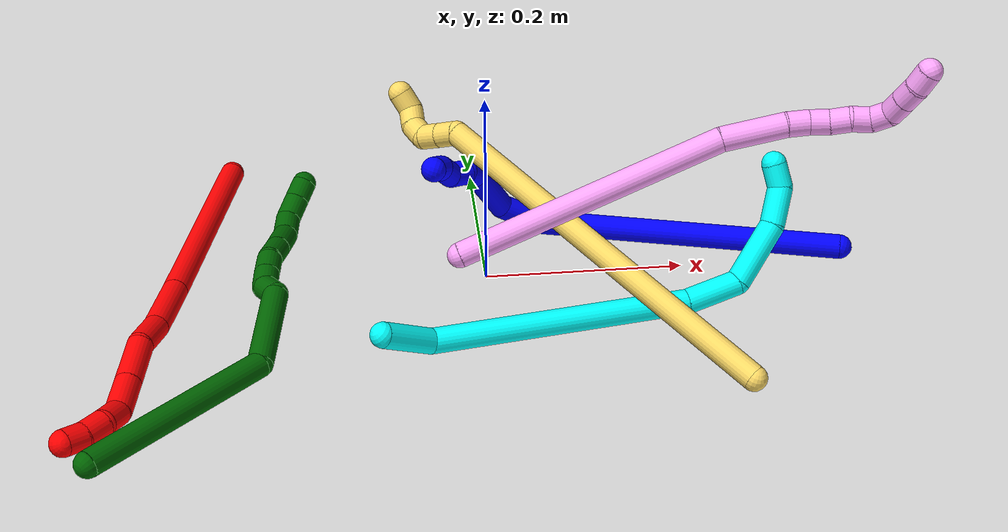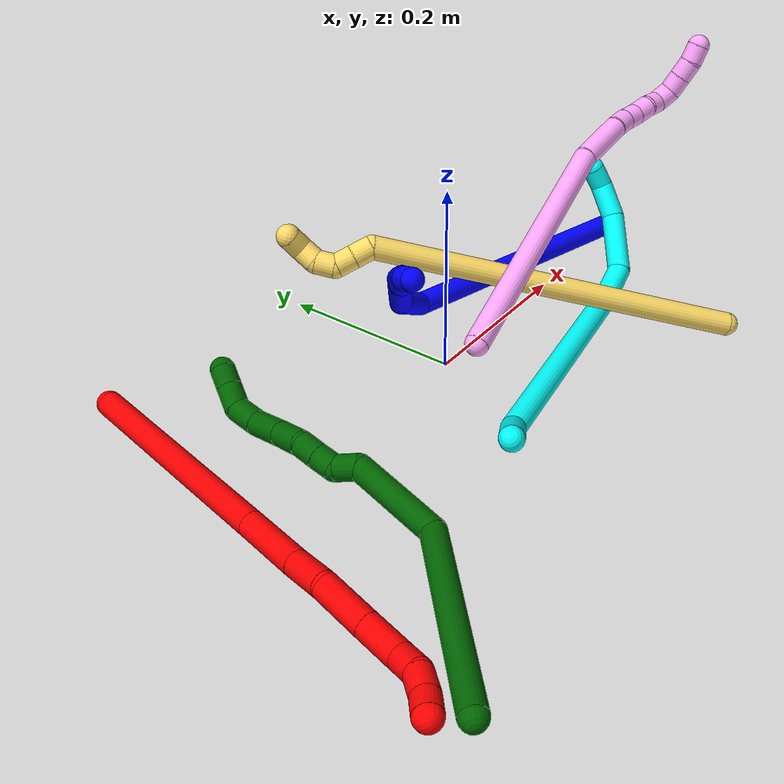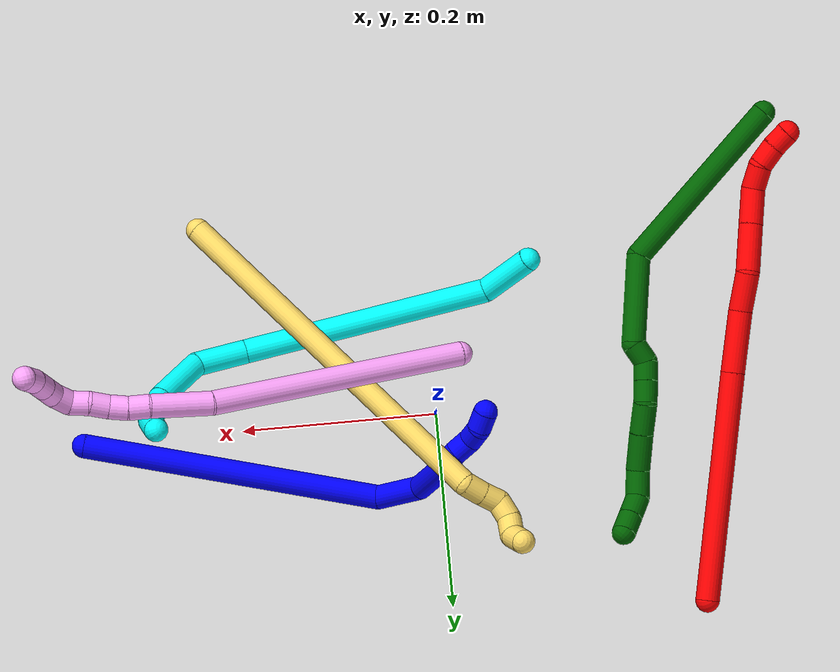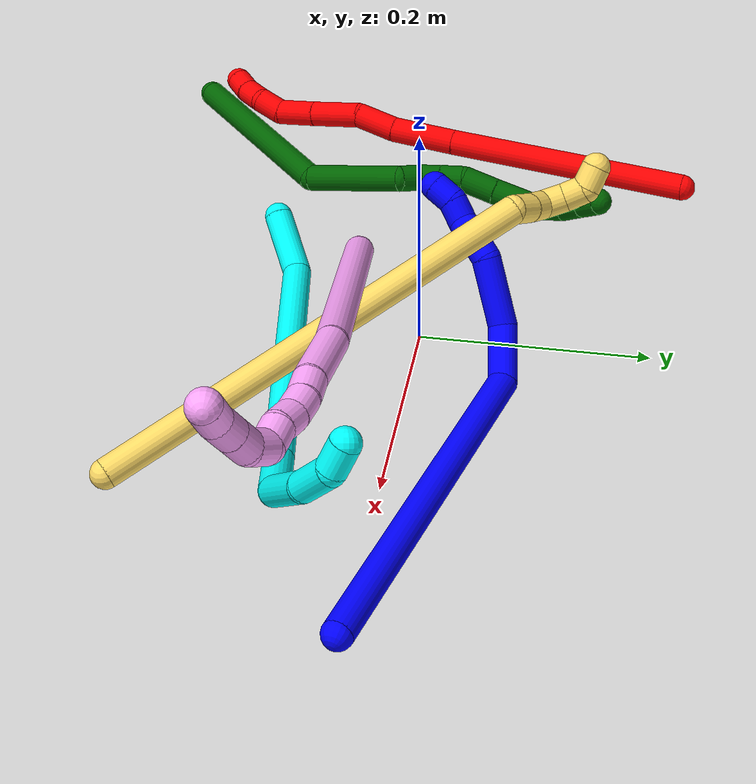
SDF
<sdf version="1.7">
 <world name="default">
  <plugin name="TubeGeneratorPlugin" filename="libtube_generator_plugin.so"/>
  <model name="photoneo_s_sensor">
   <static>1</static>
   <pose>0 0 2 1.57079 1.57079 3.14159</pose>
   <link name="link">
    <inertial><mass>0.1</mass></inertial>
    <sensor name="sensor" type="depth">
     <update_rate>30</update_rate>
     <camera>
      <horizontal_fov>1.22</horizontal_fov>
      <image><width>1920</width><height>1200</height><format>B8G8R8</format></image>
      <clip><near>0.1</near><far>4</far></clip>
      <depth_camera><output>points</output></depth_camera>
     </camera>
     <plugin name="camera_plugin" filename="libgazebo_ros_depth_camera.so">
      <baseline>0.2</baseline>
      <alwaysOn>1</alwaysOn>
      <updateRate>0.0</updateRate>
      <cameraName>camera_ir</cameraName>
      <imageTopicName>/camera/color/image_raw</imageTopicName>
      <cameraInfoTopicName>/camera/color/camera_info</cameraInfoTopicName>
      <depthImageTopicName>/camera/depth/image_raw</depthImageTopicName>
      <depthImageCameraInfoTopicName>/camera/depth/camera_info</depthImageCameraInfoTopicName>
      <pointCloudTopicName>/camera/depth/points</pointCloudTopicName>
      <frameName>fr_optical</frameName>
      <pointCloudCutoff>0.1</pointCloudCutoff>
      <pointCloudCutoffMax>2.0</pointCloudCutoffMax>
      <distortionK1>0</distortionK1>
      <distortionK2>0</distortionK2>
      <distortionK3>0</distortionK3>
      <distortionT1>0</distortionT1>
      <distortionT2>0</distortionT2>
      <CxPrime>0</CxPrime>
      <Cx>0</Cx>
      <Cy>0</Cy>
      <focalLength>0</focalLength>
      <hackBaseline>0</hackBaseline>
     </plugin>
    </sensor>
   </link>
  </model>
  <gravity>0 0 -9.8</gravity>
  <magnetic_field>6e-06 2.3e-05 -4.2e-05</magnetic_field>
  <atmosphere type="adiabatic"/>
  <physics name="default_physics" default="0" type="ode">
   <max_step_size>0.003</max_step_size>
   <real_time_factor>1</real_time_factor>
   <real_time_update_rate>1000</real_time_update_rate>
   <max_contacts>10000</max_contacts>
   <ode>
    <solver>
     <type>quick</type>
     <iters>100</iters>
     <sor>1.3</sor>
     <use_dynamic_moi_rescaling>0</use_dynamic_moi_rescaling>
    </solver>
    <constraints>
     <contact_max_correcting_vel>0</contact_max_correcting_vel>
     <contact_surface_layer>0.001</contact_surface_layer>
     <cfm>0</cfm>
     <erp>0.2</erp>
    </constraints>
   </ode>
  </physics>
  <scene><ambient>0.4 0.4 0.4 1</ambient><background>0.7 0.7 0.7 1</background><shadows>0</shadows></scene>
  <audio><device>default</device></audio>
  <spherical_coordinates>
   <surface_model>EARTH_WGS84</surface_model>
   <latitude_deg>0</latitude_deg>
   <longitude_deg>0</longitude_deg>
   <elevation>0</elevation>
   <heading_deg>0</heading_deg>
  </spherical_coordinates>
  <model name="bin">
   <static>1</static>
   <link name="bottom">
    <collision name="collision-bottom">
     <pose>0 0 -0.01 0 -0 0</pose>
     <geometry><box><size>0.8 0.6 0.02</size></box></geometry>
     <surface>
      <friction><ode><mu>100</mu><mu2>100</mu2></ode></friction>
      <contact><collide_bitmask>65535</collide_bitmask></contact>
     </surface>
    </collision>
   </link>
   <link name="west_wall">
    <collision name="collision-west_wall">
     <pose>-0.41 0 0.1 0 -0 0</pose>
     <geometry><box><size>0.02 0.6 0.2</size></box></geometry>
     <surface>
      <friction><ode><mu>100</mu><mu2>100</mu2></ode></friction>
      <contact><collide_bitmask>65535</collide_bitmask></contact>
     </surface>
    </collision>
   </link>
   <link name="east_wall">
    <collision name="collision-east_wall">
     <pose>0.41 0 0.1 0 -0 0</pose>
     <geometry><box><size>0.02 0.6 0.2</size></box></geometry>
     <surface>
      <friction><ode><mu>100</mu><mu2>100</mu2></ode></friction>
      <contact><collide_bitmask>65535</collide_bitmask></contact>
     </surface>
    </collision>
   </link>
   <link name="south_wall">
    <collision name="collision-south_wall">
     <pose>0 -0.31 0.1 0 -0 0</pose>
     <geometry><box><size>0.8 0.02 0.2</size></box></geometry>
     <surface>
      <friction><ode><mu>100</mu><mu2>100</mu2></ode></friction>
      <contact><collide_bitmask>65535</collide_bitmask></contact>
     </surface>
    </collision>
   </link>
   <link name="north_wall">
    <collision name="collision-north_wall">
     <pose>0 0.31 0.1 0 -0 0</pose>
     <geometry><box><size>0.8 0.02 0.2</size></box></geometry>
     <surface>
      <friction><ode><mu>100</mu><mu2>100</mu2></ode></friction>
      <contact><collide_bitmask>65535</collide_bitmask></contact>
     </surface>
    </collision>
   </link>
  </model>
  <model name="1">
   <static>0</static>
   <link name="1">
    <collision name="collision-cylinder-e_1_1_4">
     <pose>0.047814 -0.007924 -0.14666 3.08761 0.314728 2.80455</pose>
     <geometry><cylinder><radius>0.0125</radius><length>0.308921</length></cylinder></geometry>
     <surface>
      <friction><ode><mu>1.16</mu><mu2>1.16</mu2><slip1>0</slip1><slip2>0</slip2></ode></friction>
      <contact><ode><kp>1e+06</kp><kd>1</kd><max_vel>0</max_vel><min_depth>0.001</min_depth></ode></contact>
     </surface>
    </collision>
    <visual name="visual-cylinder-e_1_1_4">
     <pose>0.047814 -0.007924 -0.14666 3.08761 0.314728 2.80455</pose>
     <geometry><cylinder><radius>0.0125</radius><length>0.308921</length></cylinder></geometry>
     <material><ambient>0 0 1 1</ambient></material>
    </visual>
    <collision name="collision-cylinder-e_2_4_5">
     <pose>0.08801 -0.021388 -0.316704 2.90899 -0.307 -1.84806</pose>
     <geometry><cylinder><radius>0.0125</radius><length>0.050421</length></cylinder></geometry>
     <surface>
      <friction><ode><mu>1.16</mu><mu2>1.16</mu2><slip1>0</slip1><slip2>0</slip2></ode></friction>
      <contact><ode><kp>1e+06</kp><kd>1</kd><max_vel>0</max_vel><min_depth>0.001</min_depth></ode></contact>
     </surface>
    </collision>
    <visual name="visual-cylinder-e_2_4_5">
     <pose>0.08801 -0.021388 -0.316704 2.90899 -0.307 -1.84806</pose>
     <geometry><cylinder><radius>0.0125</radius><length>0.050421</length></cylinder></geometry>
     <material><ambient>0 0 1 1</ambient></material>
    </visual>
    <collision name="collision-cylinder-e_3_5_6">
     <pose>0.05775 -0.032829 -0.358565 2.83245 -0.862471 -2.48856</pose>
     <geometry><cylinder><radius>0.0125</radius><length>0.059626</length></cylinder></geometry>
     <surface>
      <friction><ode><mu>1.16</mu><mu2>1.16</mu2><slip1>0</slip1><slip2>0</slip2></ode></friction>
      <contact><ode><kp>1e+06</kp><kd>1</kd><max_vel>0</max_vel><min_depth>0.001</min_depth></ode></contact>
     </surface>
    </collision>
    <visual name="visual-cylinder-e_3_5_6">
     <pose>0.05775 -0.032829 -0.358565 2.83245 -0.862471 -2.48856</pose>
     <geometry><cylinder><radius>0.0125</radius><length>0.059626</length></cylinder></geometry>
     <material><ambient>0 0 1 1</ambient></material>
    </visual>
    <collision name="collision-cylinder-e_4_6_7">
     <pose>0.028992 -0.044445 -0.382789 2.35913 -0.646429 -1.36408</pose>
     <geometry><cylinder><radius>0.0125</radius><length>0.020311</length></cylinder></geometry>
     <surface>
      <friction><ode><mu>1.16</mu><mu2>1.16</mu2><slip1>0</slip1><slip2>0</slip2></ode></friction>
      <contact><ode><kp>1e+06</kp><kd>1</kd><max_vel>0</max_vel><min_depth>0.001</min_depth></ode></contact>
     </surface>
    </collision>
    <visual name="visual-cylinder-e_4_6_7">
     <pose>0.028992 -0.044445 -0.382789 2.35913 -0.646429 -1.36408</pose>
     <geometry><cylinder><radius>0.0125</radius><length>0.020311</length></cylinder></geometry>
     <material><ambient>0 0 1 1</ambient></material>
    </visual>
    <collision name="collision-cylinder-e_5_7_8">
     <pose>0.020872 -0.057264 -0.395498 2.34597 -0.198681 -0.465761</pose>
     <geometry><cylinder><radius>0.0125</radius><length>0.02029</length></cylinder></geometry>
     <surface>
      <friction><ode><mu>1.16</mu><mu2>1.16</mu2><slip1>0</slip1><slip2>0</slip2></ode></friction>
      <contact><ode><kp>1e+06</kp><kd>1</kd><max_vel>0</max_vel><min_depth>0.001</min_depth></ode></contact>
     </surface>
    </collision>
    <visual name="visual-cylinder-e_5_7_8">
     <pose>0.020872 -0.057264 -0.395498 2.34597 -0.198681 -0.465761</pose>
     <geometry><cylinder><radius>0.0125</radius><length>0.02029</length></cylinder></geometry>
     <material><ambient>0 0 1 1</ambient></material>
    </visual>
    <collision name="collision-cylinder-e_6_8_9">
     <pose>0.011602 -0.068623 -0.408192 2.50315 -0.794273 -1.80677</pose>
     <geometry><cylinder><radius>0.0125</radius><length>0.020376</length></cylinder></geometry>
     <surface>
      <friction><ode><mu>1.16</mu><mu2>1.16</mu2><slip1>0</slip1><slip2>0</slip2></ode></friction>
      <contact><ode><kp>1e+06</kp><kd>1</kd><max_vel>0</max_vel><min_depth>0.001</min_depth></ode></contact>
     </surface>
    </collision>
    <visual name="visual-cylinder-e_6_8_9">
     <pose>0.011602 -0.068623 -0.408192 2.50315 -0.794273 -1.80677</pose>
     <geometry><cylinder><radius>0.0125</radius><length>0.020376</length></cylinder></geometry>
     <material><ambient>0 0 1 1</ambient></material>
    </visual>
    <collision name="collision-cylinder-e_7_9_2">
     <pose>-0.001335 -0.080437 -0.417281 1.98864 -0.600958 -0.889515</pose>
     <geometry><cylinder><radius>0.0125</radius><length>0.020055</length></cylinder></geometry>
     <surface>
      <friction><ode><mu>1.16</mu><mu2>1.16</mu2><slip1>0</slip1><slip2>0</slip2></ode></friction>
      <contact><ode><kp>1e+06</kp><kd>1</kd><max_vel>0</max_vel><min_depth>0.001</min_depth></ode></contact>
     </surface>
    </collision>
    <visual name="visual-cylinder-e_7_9_2">
     <pose>-0.001335 -0.080437 -0.417281 1.98864 -0.600958 -0.889515</pose>
     <geometry><cylinder><radius>0.0125</radius><length>0.020055</length></cylinder></geometry>
     <material><ambient>0 0 1 1</ambient></material>
    </visual>
    <collision name="collision-sphere-2">
     <pose>-0.007005 -0.087996 -0.420638 0 -0 0</pose>
     <geometry><sphere><radius>0.0125</radius></sphere></geometry>
     <surface>
      <friction><ode><mu>1.16</mu><mu2>1.16</mu2><slip1>0</slip1><slip2>0</slip2></ode></friction>
      <contact><ode><kp>1e+06</kp><kd>1</kd><max_vel>0</max_vel><min_depth>0.001</min_depth></ode></contact>
     </surface>
    </collision>
    <visual name="visual-sphere-2">
     <pose>-0.007005 -0.087996 -0.420638 0 -0 0</pose>
     <geometry><sphere><radius>0.0125</radius></sphere></geometry>
     <material><ambient>0 0 1 1</ambient></material>
    </visual>
    <collision name="collision-sphere-9">
     <pose>0.004335 -0.072878 -0.413925 0 -0 0</pose>
     <geometry><sphere><radius>0.0125</radius></sphere></geometry>
     <surface>
      <friction><ode><mu>1.16</mu><mu2>1.16</mu2><slip1>0</slip1><slip2>0</slip2></ode></friction>
      <contact><ode><kp>1e+06</kp><kd>1</kd><max_vel>0</max_vel><min_depth>0.001</min_depth></ode></contact>
     </surface>
    </collision>
    <visual name="visual-sphere-9">
     <pose>0.004335 -0.072878 -0.413925 0 -0 0</pose>
     <geometry><sphere><radius>0.0125</radius></sphere></geometry>
     <material><ambient>0 0 1 1</ambient></material>
    </visual>
    <collision name="collision-sphere-4">
     <pose>0.095629 -0.015849 -0.29332 0 -0 0</pose>
     <geometry><sphere><radius>0.0125</radius></sphere></geometry>
     <surface>
      <friction><ode><mu>1.16</mu><mu2>1.16</mu2><slip1>0</slip1><slip2>0</slip2></ode></friction>
      <contact><ode><kp>1e+06</kp><kd>1</kd><max_vel>0</max_vel><min_depth>0.001</min_depth></ode></contact>
     </surface>
    </collision>
    <visual name="visual-sphere-4">
     <pose>0.095629 -0.015849 -0.29332 0 -0 0</pose>
     <geometry><sphere><radius>0.0125</radius></sphere></geometry>
     <material><ambient>0 0 1 1</ambient></material>
    </visual>
    <collision name="collision-sphere-1">
     <geometry><sphere><radius>0.0125</radius></sphere></geometry>
     <surface>
      <friction><ode><mu>1.16</mu><mu2>1.16</mu2><slip1>0</slip1><slip2>0</slip2></ode></friction>
      <contact><ode><kp>1e+06</kp><kd>1</kd><max_vel>0</max_vel><min_depth>0.001</min_depth></ode></contact>
     </surface>
    </collision>
    <visual name="visual-sphere-1">
     <geometry><sphere><radius>0.0125</radius></sphere></geometry>
     <material><ambient>0 0 1 1</ambient></material>
    </visual>
    <collision name="collision-sphere-8">
     <pose>0.01887 -0.064368 -0.402458 0 -0 0</pose>
     <geometry><sphere><radius>0.0125</radius></sphere></geometry>
     <surface>
      <friction><ode><mu>1.16</mu><mu2>1.16</mu2><slip1>0</slip1><slip2>0</slip2></ode></friction>
      <contact><ode><kp>1e+06</kp><kd>1</kd><max_vel>0</max_vel><min_depth>0.001</min_depth></ode></contact>
     </surface>
    </collision>
    <visual name="visual-sphere-8">
     <pose>0.01887 -0.064368 -0.402458 0 -0 0</pose>
     <geometry><sphere><radius>0.0125</radius></sphere></geometry>
     <material><ambient>0 0 1 1</ambient></material>
    </visual>
    <collision name="collision-sphere-5">
     <pose>0.080392 -0.026928 -0.340089 0 -0 0</pose>
     <geometry><sphere><radius>0.0125</radius></sphere></geometry>
     <surface>
      <friction><ode><mu>1.16</mu><mu2>1.16</mu2><slip1>0</slip1><slip2>0</slip2></ode></friction>
      <contact><ode><kp>1e+06</kp><kd>1</kd><max_vel>0</max_vel><min_depth>0.001</min_depth></ode></contact>
     </surface>
    </collision>
    <visual name="visual-sphere-5">
     <pose>0.080392 -0.026928 -0.340089 0 -0 0</pose>
     <geometry><sphere><radius>0.0125</radius></sphere></geometry>
     <material><ambient>0 0 1 1</ambient></material>
    </visual>
    <collision name="collision-sphere-6">
     <pose>0.035109 -0.03873 -0.37704 0 -0 0</pose>
     <geometry><sphere><radius>0.0125</radius></sphere></geometry>
     <surface>
      <friction><ode><mu>1.16</mu><mu2>1.16</mu2><slip1>0</slip1><slip2>0</slip2></ode></friction>
      <contact><ode><kp>1e+06</kp><kd>1</kd><max_vel>0</max_vel><min_depth>0.001</min_depth></ode></contact>
     </surface>
    </collision>
    <visual name="visual-sphere-6">
     <pose>0.035109 -0.03873 -0.37704 0 -0 0</pose>
     <geometry><sphere><radius>0.0125</radius></sphere></geometry>
     <material><ambient>0 0 1 1</ambient></material>
    </visual>
    <collision name="collision-sphere-7">
     <pose>0.022875 -0.05016 -0.388538 0 -0 0</pose>
     <geometry><sphere><radius>0.0125</radius></sphere></geometry>
     <surface>
      <friction><ode><mu>1.16</mu><mu2>1.16</mu2><slip1>0</slip1><slip2>0</slip2></ode></friction>
      <contact><ode><kp>1e+06</kp><kd>1</kd><max_vel>0</max_vel><min_depth>0.001</min_depth></ode></contact>
     </surface>
    </collision>
    <visual name="visual-sphere-7">
     <pose>0.022875 -0.05016 -0.388538 0 -0 0</pose>
     <geometry><sphere><radius>0.0125</radius></sphere></geometry>
     <material><ambient>0 0 1 1</ambient></material>
    </visual>
    <inertial>
     <pose>0.047748 -0.02112 -0.23028 0 -0 0</pose>
     <mass>0.5</mass>
     <inertia>
      <ixx>-0.001475</ixx>
      <ixy>0</ixy>
      <ixz>0</ixz>
      <iyy>0.003109</iyy>
      <iyz>0</iyz>
      <izz>-0.000638</izz>
     </inertia>
    </inertial>
   </link>
   <pose>0.364749 -0.000209 0.012032 2.41701 1.14424 2.1467</pose>
  </model>
  <model name="2">
   <static>0</static>
   <link name="2">
    <collision name="collision-cylinder-e_1_1_4">
     <pose>-0.014287 -0.086491 0.079296 0.828771 -0.121158 -0.053345</pose>
     <geometry><cylinder><radius>0.0125</radius><length>0.236411</length></cylinder></geometry>
     <surface>
      <friction><ode><mu>1.16</mu><mu2>1.16</mu2><slip1>0</slip1><slip2>0</slip2></ode></friction>
      <contact><ode><kp>1e+06</kp><kd>1</kd><max_vel>0</max_vel><min_depth>0.001</min_depth></ode></contact>
     </surface>
    </collision>
    <visual name="visual-cylinder-e_1_1_4">
     <pose>-0.014287 -0.086491 0.079296 0.828771 -0.121158 -0.053345</pose>
     <geometry><cylinder><radius>0.0125</radius><length>0.236411</length></cylinder></geometry>
     <material><ambient>1 0 0 1</ambient></material>
    </visual>
    <collision name="collision-cylinder-e_2_4_5">
     <pose>-0.033037 -0.196621 0.180321 0.827479 -0.138139 -0.060732</pose>
     <geometry><cylinder><radius>0.0125</radius><length>0.064837</length></cylinder></geometry>
     <surface>
      <friction><ode><mu>1.16</mu><mu2>1.16</mu2><slip1>0</slip1><slip2>0</slip2></ode></friction>
      <contact><ode><kp>1e+06</kp><kd>1</kd><max_vel>0</max_vel><min_depth>0.001</min_depth></ode></contact>
     </surface>
    </collision>
    <visual name="visual-cylinder-e_2_4_5">
     <pose>-0.033037 -0.196621 0.180321 0.827479 -0.138139 -0.060732</pose>
     <geometry><cylinder><radius>0.0125</radius><length>0.064837</length></cylinder></geometry>
     <material><ambient>1 0 0 1</ambient></material>
    </visual>
    <collision name="collision-cylinder-e_3_5_6">
     <pose>-0.042996 -0.233143 0.216737 0.720036 -0.274172 -0.103763</pose>
     <geometry><cylinder><radius>0.0125</radius><length>0.040587</length></cylinder></geometry>
     <surface>
      <friction><ode><mu>1.16</mu><mu2>1.16</mu2><slip1>0</slip1><slip2>0</slip2></ode></friction>
      <contact><ode><kp>1e+06</kp><kd>1</kd><max_vel>0</max_vel><min_depth>0.001</min_depth></ode></contact>
     </surface>
    </collision>
    <visual name="visual-cylinder-e_3_5_6">
     <pose>-0.042996 -0.233143 0.216737 0.720036 -0.274172 -0.103763</pose>
     <geometry><cylinder><radius>0.0125</radius><length>0.040587</length></cylinder></geometry>
     <material><ambient>1 0 0 1</ambient></material>
    </visual>
    <collision name="collision-cylinder-e_4_6_7">
     <pose>-0.048608 -0.266026 0.246294 0.931464 -0.004736 -0.00238</pose>
     <geometry><cylinder><radius>0.0125</radius><length>0.049846</length></cylinder></geometry>
     <surface>
      <friction><ode><mu>1.16</mu><mu2>1.16</mu2><slip1>0</slip1><slip2>0</slip2></ode></friction>
      <contact><ode><kp>1e+06</kp><kd>1</kd><max_vel>0</max_vel><min_depth>0.001</min_depth></ode></contact>
     </surface>
    </collision>
    <visual name="visual-cylinder-e_4_6_7">
     <pose>-0.048608 -0.266026 0.246294 0.931464 -0.004736 -0.00238</pose>
     <geometry><cylinder><radius>0.0125</radius><length>0.049846</length></cylinder></geometry>
     <material><ambient>1 0 0 1</ambient></material>
    </visual>
    <collision name="collision-cylinder-e_5_7_8">
     <pose>-0.049069 -0.301284 0.27288 0.916012 -0.017835 -0.008792</pose>
     <geometry><cylinder><radius>0.0125</radius><length>0.038479</length></cylinder></geometry>
     <surface>
      <friction><ode><mu>1.16</mu><mu2>1.16</mu2><slip1>0</slip1><slip2>0</slip2></ode></friction>
      <contact><ode><kp>1e+06</kp><kd>1</kd><max_vel>0</max_vel><min_depth>0.001</min_depth></ode></contact>
     </surface>
    </collision>
    <visual name="visual-cylinder-e_5_7_8">
     <pose>-0.049069 -0.301284 0.27288 0.916012 -0.017835 -0.008792</pose>
     <geometry><cylinder><radius>0.0125</radius><length>0.038479</length></cylinder></geometry>
     <material><ambient>1 0 0 1</ambient></material>
    </visual>
    <collision name="collision-cylinder-e_6_8_9">
     <pose>-0.054671 -0.324096 0.29375 0.689818 -0.41706 -0.151755</pose>
     <geometry><cylinder><radius>0.0125</radius><length>0.025965</length></cylinder></geometry>
     <surface>
      <friction><ode><mu>1.16</mu><mu2>1.16</mu2><slip1>0</slip1><slip2>0</slip2></ode></friction>
      <contact><ode><kp>1e+06</kp><kd>1</kd><max_vel>0</max_vel><min_depth>0.001</min_depth></ode></contact>
     </surface>
    </collision>
    <visual name="visual-cylinder-e_6_8_9">
     <pose>-0.054671 -0.324096 0.29375 0.689818 -0.41706 -0.151755</pose>
     <geometry><cylinder><radius>0.0125</radius><length>0.025965</length></cylinder></geometry>
     <material><ambient>1 0 0 1</ambient></material>
    </visual>
    <collision name="collision-cylinder-e_7_9_10">
     <pose>-0.066069 -0.340493 0.307223 1.11663 -0.557724 -0.353934</pose>
     <geometry><cylinder><radius>0.0125</radius><length>0.023197</length></cylinder></geometry>
     <surface>
      <friction><ode><mu>1.16</mu><mu2>1.16</mu2><slip1>0</slip1><slip2>0</slip2></ode></friction>
      <contact><ode><kp>1e+06</kp><kd>1</kd><max_vel>0</max_vel><min_depth>0.001</min_depth></ode></contact>
     </surface>
    </collision>
    <visual name="visual-cylinder-e_7_9_10">
     <pose>-0.066069 -0.340493 0.307223 1.11663 -0.557724 -0.353934</pose>
     <geometry><cylinder><radius>0.0125</radius><length>0.023197</length></cylinder></geometry>
     <material><ambient>1 0 0 1</ambient></material>
    </visual>
    <collision name="collision-cylinder-e_8_10_2">
     <pose>-0.079262 -0.356044 0.315022 1.09206 -0.751013 -0.470231</pose>
     <geometry><cylinder><radius>0.0125</radius><length>0.020678</length></cylinder></geometry>
     <surface>
      <friction><ode><mu>1.16</mu><mu2>1.16</mu2><slip1>0</slip1><slip2>0</slip2></ode></friction>
      <contact><ode><kp>1e+06</kp><kd>1</kd><max_vel>0</max_vel><min_depth>0.001</min_depth></ode></contact>
     </surface>
    </collision>
    <visual name="visual-cylinder-e_8_10_2">
     <pose>-0.079262 -0.356044 0.315022 1.09206 -0.751013 -0.470231</pose>
     <geometry><cylinder><radius>0.0125</radius><length>0.020678</length></cylinder></geometry>
     <material><ambient>1 0 0 1</ambient></material>
    </visual>
    <collision name="collision-sphere-2">
     <pose>-0.086317 -0.362752 0.318504 0 -0 0</pose>
     <geometry><sphere><radius>0.0125</radius></sphere></geometry>
     <surface>
      <friction><ode><mu>1.16</mu><mu2>1.16</mu2><slip1>0</slip1><slip2>0</slip2></ode></friction>
      <contact><ode><kp>1e+06</kp><kd>1</kd><max_vel>0</max_vel><min_depth>0.001</min_depth></ode></contact>
     </surface>
    </collision>
    <visual name="visual-sphere-2">
     <pose>-0.086317 -0.362752 0.318504 0 -0 0</pose>
     <geometry><sphere><radius>0.0125</radius></sphere></geometry>
     <material><ambient>1 0 0 1</ambient></material>
    </visual>
    <collision name="collision-sphere-10">
     <pose>-0.072207 -0.349337 0.311541 0 -0 0</pose>
     <geometry><sphere><radius>0.0125</radius></sphere></geometry>
     <surface>
      <friction><ode><mu>1.16</mu><mu2>1.16</mu2><slip1>0</slip1><slip2>0</slip2></ode></friction>
      <contact><ode><kp>1e+06</kp><kd>1</kd><max_vel>0</max_vel><min_depth>0.001</min_depth></ode></contact>
     </surface>
    </collision>
    <visual name="visual-sphere-10">
     <pose>-0.072207 -0.349337 0.311541 0 -0 0</pose>
     <geometry><sphere><radius>0.0125</radius></sphere></geometry>
     <material><ambient>1 0 0 1</ambient></material>
    </visual>
    <collision name="collision-sphere-9">
     <pose>-0.05993 -0.33165 0.302906 0 -0 0</pose>
     <geometry><sphere><radius>0.0125</radius></sphere></geometry>
     <surface>
      <friction><ode><mu>1.16</mu><mu2>1.16</mu2><slip1>0</slip1><slip2>0</slip2></ode></friction>
      <contact><ode><kp>1e+06</kp><kd>1</kd><max_vel>0</max_vel><min_depth>0.001</min_depth></ode></contact>
     </surface>
    </collision>
    <visual name="visual-sphere-9">
     <pose>-0.05993 -0.33165 0.302906 0 -0 0</pose>
     <geometry><sphere><radius>0.0125</radius></sphere></geometry>
     <material><ambient>1 0 0 1</ambient></material>
    </visual>
    <collision name="collision-sphere-4">
     <pose>-0.028573 -0.172981 0.158591 0 -0 0</pose>
     <geometry><sphere><radius>0.0125</radius></sphere></geometry>
     <surface>
      <friction><ode><mu>1.16</mu><mu2>1.16</mu2><slip1>0</slip1><slip2>0</slip2></ode></friction>
      <contact><ode><kp>1e+06</kp><kd>1</kd><max_vel>0</max_vel><min_depth>0.001</min_depth></ode></contact>
     </surface>
    </collision>
    <visual name="visual-sphere-4">
     <pose>-0.028573 -0.172981 0.158591 0 -0 0</pose>
     <geometry><sphere><radius>0.0125</radius></sphere></geometry>
     <material><ambient>1 0 0 1</ambient></material>
    </visual>
    <collision name="collision-sphere-1">
     <geometry><sphere><radius>0.0125</radius></sphere></geometry>
     <surface>
      <friction><ode><mu>1.16</mu><mu2>1.16</mu2><slip1>0</slip1><slip2>0</slip2></ode></friction>
      <contact><ode><kp>1e+06</kp><kd>1</kd><max_vel>0</max_vel><min_depth>0.001</min_depth></ode></contact>
     </surface>
    </collision>
    <visual name="visual-sphere-1">
     <geometry><sphere><radius>0.0125</radius></sphere></geometry>
     <material><ambient>1 0 0 1</ambient></material>
    </visual>
    <collision name="collision-sphere-8">
     <pose>-0.049412 -0.316543 0.284594 0 -0 0</pose>
     <geometry><sphere><radius>0.0125</radius></sphere></geometry>
     <surface>
      <friction><ode><mu>1.16</mu><mu2>1.16</mu2><slip1>0</slip1><slip2>0</slip2></ode></friction>
      <contact><ode><kp>1e+06</kp><kd>1</kd><max_vel>0</max_vel><min_depth>0.001</min_depth></ode></contact>
     </surface>
    </collision>
    <visual name="visual-sphere-8">
     <pose>-0.049412 -0.316543 0.284594 0 -0 0</pose>
     <geometry><sphere><radius>0.0125</radius></sphere></geometry>
     <material><ambient>1 0 0 1</ambient></material>
    </visual>
    <collision name="collision-sphere-5">
     <pose>-0.037501 -0.220261 0.202051 0 -0 0</pose>
     <geometry><sphere><radius>0.0125</radius></sphere></geometry>
     <surface>
      <friction><ode><mu>1.16</mu><mu2>1.16</mu2><slip1>0</slip1><slip2>0</slip2></ode></friction>
      <contact><ode><kp>1e+06</kp><kd>1</kd><max_vel>0</max_vel><min_depth>0.001</min_depth></ode></contact>
     </surface>
    </collision>
    <visual name="visual-sphere-5">
     <pose>-0.037501 -0.220261 0.202051 0 -0 0</pose>
     <geometry><sphere><radius>0.0125</radius></sphere></geometry>
     <material><ambient>1 0 0 1</ambient></material>
    </visual>
    <collision name="collision-sphere-6">
     <pose>-0.04849 -0.246025 0.231424 0 -0 0</pose>
     <geometry><sphere><radius>0.0125</radius></sphere></geometry>
     <surface>
      <friction><ode><mu>1.16</mu><mu2>1.16</mu2><slip1>0</slip1><slip2>0</slip2></ode></friction>
      <contact><ode><kp>1e+06</kp><kd>1</kd><max_vel>0</max_vel><min_depth>0.001</min_depth></ode></contact>
     </surface>
    </collision>
    <visual name="visual-sphere-6">
     <pose>-0.04849 -0.246025 0.231424 0 -0 0</pose>
     <geometry><sphere><radius>0.0125</radius></sphere></geometry>
     <material><ambient>1 0 0 1</ambient></material>
    </visual>
    <collision name="collision-sphere-7">
     <pose>-0.048726 -0.286026 0.261165 0 -0 0</pose>
     <geometry><sphere><radius>0.0125</radius></sphere></geometry>
     <surface>
      <friction><ode><mu>1.16</mu><mu2>1.16</mu2><slip1>0</slip1><slip2>0</slip2></ode></friction>
      <contact><ode><kp>1e+06</kp><kd>1</kd><max_vel>0</max_vel><min_depth>0.001</min_depth></ode></contact>
     </surface>
    </collision>
    <visual name="visual-sphere-7">
     <pose>-0.048726 -0.286026 0.261165 0 -0 0</pose>
     <geometry><sphere><radius>0.0125</radius></sphere></geometry>
     <material><ambient>1 0 0 1</ambient></material>
    </visual>
    <inertial>
     <pose>-0.032334 -0.182375 0.166559 0 -0 0</pose>
     <mass>0.5</mass>
     <inertia>
      <ixx>0.001086</ixx>
      <ixy>0</ixy>
      <ixz>0</ixz>
      <iyy>0.000702</iyy>
      <iyz>0</iyz>
      <izz>0.001022</izz>
     </inertia>
    </inertial>
   </link>
   <pose>-0.262022 0.21742 0.012309 0.810069 0.576184 -0.06406</pose>
  </model>
  <model name="3">
   <static>0</static>
   <link name="3">
    <collision name="collision-cylinder-e_1_1_4">
     <pose>0.011598 0.005868 -0.026948 -2.9272 0.39806 -2.16141</pose>
     <geometry><cylinder><radius>0.0125</radius><length>0.059838</length></cylinder></geometry>
     <surface>
      <friction><ode><mu>1.16</mu><mu2>1.16</mu2><slip1>0</slip1><slip2>0</slip2></ode></friction>
      <contact><ode><kp>1e+06</kp><kd>1</kd><max_vel>0</max_vel><min_depth>0.001</min_depth></ode></contact>
     </surface>
    </collision>
    <visual name="visual-cylinder-e_1_1_4">
     <pose>0.011598 0.005868 -0.026948 -2.9272 0.39806 -2.16141</pose>
     <geometry><cylinder><radius>0.0125</radius><length>0.059838</length></cylinder></geometry>
     <material><ambient>0.003922 1 0.996078 1</ambient></material>
    </visual>
    <collision name="collision-cylinder-e_2_4_5">
     <pose>0.117441 -0.016031 -0.136267 2.81647 0.825788 2.42513</pose>
     <geometry><cylinder><radius>0.0125</radius><length>0.256423</length></cylinder></geometry>
     <surface>
      <friction><ode><mu>1.16</mu><mu2>1.16</mu2><slip1>0</slip1><slip2>0</slip2></ode></friction>
      <contact><ode><kp>1e+06</kp><kd>1</kd><max_vel>0</max_vel><min_depth>0.001</min_depth></ode></contact>
     </surface>
    </collision>
    <visual name="visual-cylinder-e_2_4_5">
     <pose>0.117441 -0.016031 -0.136267 2.81647 0.825788 2.42513</pose>
     <geometry><cylinder><radius>0.0125</radius><length>0.256423</length></cylinder></geometry>
     <material><ambient>0.003922 1 0.996078 1</ambient></material>
    </visual>
    <collision name="collision-cylinder-e_3_5_6">
     <pose>0.235183 -0.050186 -0.230264 2.63907 1.05681 2.31309</pose>
     <geometry><cylinder><radius>0.0125</radius><length>0.053965</length></cylinder></geometry>
     <surface>
      <friction><ode><mu>1.16</mu><mu2>1.16</mu2><slip1>0</slip1><slip2>0</slip2></ode></friction>
      <contact><ode><kp>1e+06</kp><kd>1</kd><max_vel>0</max_vel><min_depth>0.001</min_depth></ode></contact>
     </surface>
    </collision>
    <visual name="visual-cylinder-e_3_5_6">
     <pose>0.235183 -0.050186 -0.230264 2.63907 1.05681 2.31309</pose>
     <geometry><cylinder><radius>0.0125</radius><length>0.053965</length></cylinder></geometry>
     <material><ambient>0.003922 1 0.996078 1</ambient></material>
    </visual>
    <collision name="collision-cylinder-e_4_6_7">
     <pose>0.291295 -0.052246 -0.239441 -1.05603 1.41944 -0.928958</pose>
     <geometry><cylinder><radius>0.0125</radius><length>0.065985</length></cylinder></geometry>
     <surface>
      <friction><ode><mu>1.16</mu><mu2>1.16</mu2><slip1>0</slip1><slip2>0</slip2></ode></friction>
      <contact><ode><kp>1e+06</kp><kd>1</kd><max_vel>0</max_vel><min_depth>0.001</min_depth></ode></contact>
     </surface>
    </collision>
    <visual name="visual-cylinder-e_4_6_7">
     <pose>0.291295 -0.052246 -0.239441 -1.05603 1.41944 -0.928958</pose>
     <geometry><cylinder><radius>0.0125</radius><length>0.065985</length></cylinder></geometry>
     <material><ambient>0.003922 1 0.996078 1</ambient></material>
    </visual>
    <collision name="collision-cylinder-e_5_7_8">
     <pose>0.341428 -0.041335 -0.230951 -0.828158 1.09926 -0.525985</pose>
     <geometry><cylinder><radius>0.0125</radius><length>0.039327</length></cylinder></geometry>
     <surface>
      <friction><ode><mu>1.16</mu><mu2>1.16</mu2><slip1>0</slip1><slip2>0</slip2></ode></friction>
      <contact><ode><kp>1e+06</kp><kd>1</kd><max_vel>0</max_vel><min_depth>0.001</min_depth></ode></contact>
     </surface>
    </collision>
    <visual name="visual-cylinder-e_5_7_8">
     <pose>0.341428 -0.041335 -0.230951 -0.828158 1.09926 -0.525985</pose>
     <geometry><cylinder><radius>0.0125</radius><length>0.039327</length></cylinder></geometry>
     <material><ambient>0.003922 1 0.996078 1</ambient></material>
    </visual>
    <collision name="collision-cylinder-e_6_8_2">
     <pose>0.365628 -0.030925 -0.21541 -0.383152 0.577984 -0.115204</pose>
     <geometry><cylinder><radius>0.0125</radius><length>0.024462</length></cylinder></geometry>
     <surface>
      <friction><ode><mu>1.16</mu><mu2>1.16</mu2><slip1>0</slip1><slip2>0</slip2></ode></friction>
      <contact><ode><kp>1e+06</kp><kd>1</kd><max_vel>0</max_vel><min_depth>0.001</min_depth></ode></contact>
     </surface>
    </collision>
    <visual name="visual-cylinder-e_6_8_2">
     <pose>0.365628 -0.030925 -0.21541 -0.383152 0.577984 -0.115204</pose>
     <geometry><cylinder><radius>0.0125</radius><length>0.024462</length></cylinder></geometry>
     <material><ambient>0.003922 1 0.996078 1</ambient></material>
    </visual>
    <collision name="collision-sphere-2">
     <pose>0.37231 -0.027096 -0.205908 0 -0 0</pose>
     <geometry><sphere><radius>0.0125</radius></sphere></geometry>
     <surface>
      <friction><ode><mu>1.16</mu><mu2>1.16</mu2><slip1>0</slip1><slip2>0</slip2></ode></friction>
      <contact><ode><kp>1e+06</kp><kd>1</kd><max_vel>0</max_vel><min_depth>0.001</min_depth></ode></contact>
     </surface>
    </collision>
    <visual name="visual-sphere-2">
     <pose>0.37231 -0.027096 -0.205908 0 -0 0</pose>
     <geometry><sphere><radius>0.0125</radius></sphere></geometry>
     <material><ambient>0.003922 1 0.996078 1</ambient></material>
    </visual>
    <collision name="collision-sphere-4">
     <pose>0.023195 0.011735 -0.053897 0 -0 0</pose>
     <geometry><sphere><radius>0.0125</radius></sphere></geometry>
     <surface>
      <friction><ode><mu>1.16</mu><mu2>1.16</mu2><slip1>0</slip1><slip2>0</slip2></ode></friction>
      <contact><ode><kp>1e+06</kp><kd>1</kd><max_vel>0</max_vel><min_depth>0.001</min_depth></ode></contact>
     </surface>
    </collision>
    <visual name="visual-sphere-4">
     <pose>0.023195 0.011735 -0.053897 0 -0 0</pose>
     <geometry><sphere><radius>0.0125</radius></sphere></geometry>
     <material><ambient>0.003922 1 0.996078 1</ambient></material>
    </visual>
    <collision name="collision-sphere-1">
     <geometry><sphere><radius>0.0125</radius></sphere></geometry>
     <surface>
      <friction><ode><mu>1.16</mu><mu2>1.16</mu2><slip1>0</slip1><slip2>0</slip2></ode></friction>
      <contact><ode><kp>1e+06</kp><kd>1</kd><max_vel>0</max_vel><min_depth>0.001</min_depth></ode></contact>
     </surface>
    </collision>
    <visual name="visual-sphere-1">
     <geometry><sphere><radius>0.0125</radius></sphere></geometry>
     <material><ambient>0.003922 1 0.996078 1</ambient></material>
    </visual>
    <collision name="collision-sphere-8">
     <pose>0.358946 -0.034755 -0.224911 0 -0 0</pose>
     <geometry><sphere><radius>0.0125</radius></sphere></geometry>
     <surface>
      <friction><ode><mu>1.16</mu><mu2>1.16</mu2><slip1>0</slip1><slip2>0</slip2></ode></friction>
      <contact><ode><kp>1e+06</kp><kd>1</kd><max_vel>0</max_vel><min_depth>0.001</min_depth></ode></contact>
     </surface>
    </collision>
    <visual name="visual-sphere-8">
     <pose>0.358946 -0.034755 -0.224911 0 -0 0</pose>
     <geometry><sphere><radius>0.0125</radius></sphere></geometry>
     <material><ambient>0.003922 1 0.996078 1</ambient></material>
    </visual>
    <collision name="collision-sphere-5">
     <pose>0.211687 -0.043797 -0.218638 0 -0 0</pose>
     <geometry><sphere><radius>0.0125</radius></sphere></geometry>
     <surface>
      <friction><ode><mu>1.16</mu><mu2>1.16</mu2><slip1>0</slip1><slip2>0</slip2></ode></friction>
      <contact><ode><kp>1e+06</kp><kd>1</kd><max_vel>0</max_vel><min_depth>0.001</min_depth></ode></contact>
     </surface>
    </collision>
    <visual name="visual-sphere-5">
     <pose>0.211687 -0.043797 -0.218638 0 -0 0</pose>
     <geometry><sphere><radius>0.0125</radius></sphere></geometry>
     <material><ambient>0.003922 1 0.996078 1</ambient></material>
    </visual>
    <collision name="collision-sphere-6">
     <pose>0.258679 -0.056575 -0.24189 0 -0 0</pose>
     <geometry><sphere><radius>0.0125</radius></sphere></geometry>
     <surface>
      <friction><ode><mu>1.16</mu><mu2>1.16</mu2><slip1>0</slip1><slip2>0</slip2></ode></friction>
      <contact><ode><kp>1e+06</kp><kd>1</kd><max_vel>0</max_vel><min_depth>0.001</min_depth></ode></contact>
     </surface>
    </collision>
    <visual name="visual-sphere-6">
     <pose>0.258679 -0.056575 -0.24189 0 -0 0</pose>
     <geometry><sphere><radius>0.0125</radius></sphere></geometry>
     <material><ambient>0.003922 1 0.996078 1</ambient></material>
    </visual>
    <collision name="collision-sphere-7">
     <pose>0.32391 -0.047916 -0.236992 0 -0 0</pose>
     <geometry><sphere><radius>0.0125</radius></sphere></geometry>
     <surface>
      <friction><ode><mu>1.16</mu><mu2>1.16</mu2><slip1>0</slip1><slip2>0</slip2></ode></friction>
      <contact><ode><kp>1e+06</kp><kd>1</kd><max_vel>0</max_vel><min_depth>0.001</min_depth></ode></contact>
     </surface>
    </collision>
    <visual name="visual-sphere-7">
     <pose>0.32391 -0.047916 -0.236992 0 -0 0</pose>
     <geometry><sphere><radius>0.0125</radius></sphere></geometry>
     <material><ambient>0.003922 1 0.996078 1</ambient></material>
    </visual>
    <inertial>
     <pose>0.170185 -0.024595 -0.158265 0 -0 0</pose>
     <mass>0.5</mass>
     <inertia>
      <ixx>-8.8e-05</ixx>
      <ixy>0</ixy>
      <ixz>0</ixz>
      <iyy>0.001903</iyy>
      <iyz>0</iyz>
      <izz>-0.000811</izz>
     </inertia>
    </inertial>
   </link>
   <pose>-0.109185 -0.148808 0.040366 -0.205011 -0.671614 0.508326</pose>
  </model>
  <model name="4">
   <static>0</static>
   <link name="4">
    <collision name="collision-cylinder-e_1_1_4">
     <pose>0.011807 -0.000754 0.136692 0.005517 0.086161 0.000238</pose>
     <geometry><cylinder><radius>0.0125</radius><length>0.274405</length></cylinder></geometry>
     <surface>
      <friction><ode><mu>1.16</mu><mu2>1.16</mu2><slip1>0</slip1><slip2>0</slip2></ode></friction>
      <contact><ode><kp>1e+06</kp><kd>1</kd><max_vel>0</max_vel><min_depth>0.001</min_depth></ode></contact>
     </surface>
    </collision>
    <visual name="visual-cylinder-e_1_1_4">
     <pose>0.011807 -0.000754 0.136692 0.005517 0.086161 0.000238</pose>
     <geometry><cylinder><radius>0.0125</radius><length>0.274405</length></cylinder></geometry>
     <material><ambient>1 0.65098 0.996078 1</ambient></material>
    </visual>
    <collision name="collision-cylinder-e_2_4_5">
     <pose>0.026574 0.004704 0.304587 -0.196531 0.092779 -0.009153</pose>
     <geometry><cylinder><radius>0.0125</radius><length>0.063908</length></cylinder></geometry>
     <surface>
      <friction><ode><mu>1.16</mu><mu2>1.16</mu2><slip1>0</slip1><slip2>0</slip2></ode></friction>
      <contact><ode><kp>1e+06</kp><kd>1</kd><max_vel>0</max_vel><min_depth>0.001</min_depth></ode></contact>
     </surface>
    </collision>
    <visual name="visual-cylinder-e_2_4_5">
     <pose>0.026574 0.004704 0.304587 -0.196531 0.092779 -0.009153</pose>
     <geometry><cylinder><radius>0.0125</radius><length>0.063908</length></cylinder></geometry>
     <material><ambient>1 0.65098 0.996078 1</ambient></material>
    </visual>
    <collision name="collision-cylinder-e_3_5_6">
     <pose>0.02901 0.013933 0.346179 -0.282521 -0.048496 0.006898</pose>
     <geometry><cylinder><radius>0.0125</radius><length>0.021659</length></cylinder></geometry>
     <surface>
      <friction><ode><mu>1.16</mu><mu2>1.16</mu2><slip1>0</slip1><slip2>0</slip2></ode></friction>
      <contact><ode><kp>1e+06</kp><kd>1</kd><max_vel>0</max_vel><min_depth>0.001</min_depth></ode></contact>
     </surface>
    </collision>
    <visual name="visual-cylinder-e_3_5_6">
     <pose>0.02901 0.013933 0.346179 -0.282521 -0.048496 0.006898</pose>
     <geometry><cylinder><radius>0.0125</radius><length>0.021659</length></cylinder></geometry>
     <material><ambient>1 0.65098 0.996078 1</ambient></material>
    </visual>
    <collision name="collision-cylinder-e_4_6_7">
     <pose>0.029168 0.020926 0.365726 -0.409706 0.068301 -0.014196</pose>
     <geometry><cylinder><radius>0.0125</radius><length>0.020018</length></cylinder></geometry>
     <surface>
      <friction><ode><mu>1.16</mu><mu2>1.16</mu2><slip1>0</slip1><slip2>0</slip2></ode></friction>
      <contact><ode><kp>1e+06</kp><kd>1</kd><max_vel>0</max_vel><min_depth>0.001</min_depth></ode></contact>
     </surface>
    </collision>
    <visual name="visual-cylinder-e_4_6_7">
     <pose>0.029168 0.020926 0.365726 -0.409706 0.068301 -0.014196</pose>
     <geometry><cylinder><radius>0.0125</radius><length>0.020018</length></cylinder></geometry>
     <material><ambient>1 0.65098 0.996078 1</ambient></material>
    </visual>
    <collision name="collision-cylinder-e_5_7_8">
     <pose>0.03252 0.028026 0.384006 -0.329892 0.270126 -0.045232</pose>
     <geometry><cylinder><radius>0.0125</radius><length>0.020006</length></cylinder></geometry>
     <surface>
      <friction><ode><mu>1.16</mu><mu2>1.16</mu2><slip1>0</slip1><slip2>0</slip2></ode></friction>
      <contact><ode><kp>1e+06</kp><kd>1</kd><max_vel>0</max_vel><min_depth>0.001</min_depth></ode></contact>
     </surface>
    </collision>
    <visual name="visual-cylinder-e_5_7_8">
     <pose>0.03252 0.028026 0.384006 -0.329892 0.270126 -0.045232</pose>
     <geometry><cylinder><radius>0.0125</radius><length>0.020006</length></cylinder></geometry>
     <material><ambient>1 0.65098 0.996078 1</ambient></material>
    </visual>
    <collision name="collision-cylinder-e_6_8_9">
     <pose>0.035083 0.035283 0.402232 -0.426176 -0.010604 0.002294</pose>
     <geometry><cylinder><radius>0.0125</radius><length>0.020001</length></cylinder></geometry>
     <surface>
      <friction><ode><mu>1.16</mu><mu2>1.16</mu2><slip1>0</slip1><slip2>0</slip2></ode></friction>
      <contact><ode><kp>1e+06</kp><kd>1</kd><max_vel>0</max_vel><min_depth>0.001</min_depth></ode></contact>
     </surface>
    </collision>
    <visual name="visual-cylinder-e_6_8_9">
     <pose>0.035083 0.035283 0.402232 -0.426176 -0.010604 0.002294</pose>
     <geometry><cylinder><radius>0.0125</radius><length>0.020001</length></cylinder></geometry>
     <material><ambient>1 0.65098 0.996078 1</ambient></material>
    </visual>
    <collision name="collision-cylinder-e_7_9_10">
     <pose>0.041132 0.041229 0.419009 -0.231921 0.662943 -0.080137</pose>
     <geometry><cylinder><radius>0.0125</radius><length>0.020001</length></cylinder></geometry>
     <surface>
      <friction><ode><mu>1.16</mu><mu2>1.16</mu2><slip1>0</slip1><slip2>0</slip2></ode></friction>
      <contact><ode><kp>1e+06</kp><kd>1</kd><max_vel>0</max_vel><min_depth>0.001</min_depth></ode></contact>
     </surface>
    </collision>
    <visual name="visual-cylinder-e_7_9_10">
     <pose>0.041132 0.041229 0.419009 -0.231921 0.662943 -0.080137</pose>
     <geometry><cylinder><radius>0.0125</radius><length>0.020001</length></cylinder></geometry>
     <material><ambient>1 0.65098 0.996078 1</ambient></material>
    </visual>
    <collision name="collision-cylinder-e_8_10_11">
     <pose>0.055395 0.041332 0.432278 0.296287 0.945533 0.152359</pose>
     <geometry><cylinder><radius>0.0125</radius><length>0.020001</length></cylinder></geometry>
     <surface>
      <friction><ode><mu>1.16</mu><mu2>1.16</mu2><slip1>0</slip1><slip2>0</slip2></ode></friction>
      <contact><ode><kp>1e+06</kp><kd>1</kd><max_vel>0</max_vel><min_depth>0.001</min_depth></ode></contact>
     </surface>
    </collision>
    <visual name="visual-cylinder-e_8_10_11">
     <pose>0.055395 0.041332 0.432278 0.296287 0.945533 0.152359</pose>
     <geometry><cylinder><radius>0.0125</radius><length>0.020001</length></cylinder></geometry>
     <material><ambient>1 0.65098 0.996078 1</ambient></material>
    </visual>
    <collision name="collision-cylinder-e_9_11_12">
     <pose>0.071582 0.037892 0.443511 0.298081 0.940498 0.152345</pose>
     <geometry><cylinder><radius>0.0125</radius><length>0.02</length></cylinder></geometry>
     <surface>
      <friction><ode><mu>1.16</mu><mu2>1.16</mu2><slip1>0</slip1><slip2>0</slip2></ode></friction>
      <contact><ode><kp>1e+06</kp><kd>1</kd><max_vel>0</max_vel><min_depth>0.001</min_depth></ode></contact>
     </surface>
    </collision>
    <visual name="visual-cylinder-e_9_11_12">
     <pose>0.071582 0.037892 0.443511 0.298081 0.940498 0.152345</pose>
     <geometry><cylinder><radius>0.0125</radius><length>0.02</length></cylinder></geometry>
     <material><ambient>1 0.65098 0.996078 1</ambient></material>
    </visual>
    <collision name="collision-cylinder-e_10_12_2">
     <pose>0.086645 0.032821 0.455475 0.485447 0.773099 0.200886</pose>
     <geometry><cylinder><radius>0.0125</radius><length>0.02</length></cylinder></geometry>
     <surface>
      <friction><ode><mu>1.16</mu><mu2>1.16</mu2><slip1>0</slip1><slip2>0</slip2></ode></friction>
      <contact><ode><kp>1e+06</kp><kd>1</kd><max_vel>0</max_vel><min_depth>0.001</min_depth></ode></contact>
     </surface>
    </collision>
    <visual name="visual-cylinder-e_10_12_2">
     <pose>0.086645 0.032821 0.455475 0.485447 0.773099 0.200886</pose>
     <geometry><cylinder><radius>0.0125</radius><length>0.02</length></cylinder></geometry>
     <material><ambient>1 0.65098 0.996078 1</ambient></material>
    </visual>
    <collision name="collision-sphere-2">
     <pose>0.093628 0.029481 0.461806 0 -0 0</pose>
     <geometry><sphere><radius>0.0125</radius></sphere></geometry>
     <surface>
      <friction><ode><mu>1.16</mu><mu2>1.16</mu2><slip1>0</slip1><slip2>0</slip2></ode></friction>
      <contact><ode><kp>1e+06</kp><kd>1</kd><max_vel>0</max_vel><min_depth>0.001</min_depth></ode></contact>
     </surface>
    </collision>
    <visual name="visual-sphere-2">
     <pose>0.093628 0.029481 0.461806 0 -0 0</pose>
     <geometry><sphere><radius>0.0125</radius></sphere></geometry>
     <material><ambient>1 0.65098 0.996078 1</ambient></material>
    </visual>
    <collision name="collision-sphere-12">
     <pose>0.079661 0.036161 0.449145 0 -0 0</pose>
     <geometry><sphere><radius>0.0125</radius></sphere></geometry>
     <surface>
      <friction><ode><mu>1.16</mu><mu2>1.16</mu2><slip1>0</slip1><slip2>0</slip2></ode></friction>
      <contact><ode><kp>1e+06</kp><kd>1</kd><max_vel>0</max_vel><min_depth>0.001</min_depth></ode></contact>
     </surface>
    </collision>
    <visual name="visual-sphere-12">
     <pose>0.079661 0.036161 0.449145 0 -0 0</pose>
     <geometry><sphere><radius>0.0125</radius></sphere></geometry>
     <material><ambient>1 0.65098 0.996078 1</ambient></material>
    </visual>
    <collision name="collision-sphere-11">
     <pose>0.063504 0.039623 0.437877 0 -0 0</pose>
     <geometry><sphere><radius>0.0125</radius></sphere></geometry>
     <surface>
      <friction><ode><mu>1.16</mu><mu2>1.16</mu2><slip1>0</slip1><slip2>0</slip2></ode></friction>
      <contact><ode><kp>1e+06</kp><kd>1</kd><max_vel>0</max_vel><min_depth>0.001</min_depth></ode></contact>
     </surface>
    </collision>
    <visual name="visual-sphere-11">
     <pose>0.063504 0.039623 0.437877 0 -0 0</pose>
     <geometry><sphere><radius>0.0125</radius></sphere></geometry>
     <material><ambient>1 0.65098 0.996078 1</ambient></material>
    </visual>
    <collision name="collision-sphere-10">
     <pose>0.047287 0.043041 0.42668 0 -0 0</pose>
     <geometry><sphere><radius>0.0125</radius></sphere></geometry>
     <surface>
      <friction><ode><mu>1.16</mu><mu2>1.16</mu2><slip1>0</slip1><slip2>0</slip2></ode></friction>
      <contact><ode><kp>1e+06</kp><kd>1</kd><max_vel>0</max_vel><min_depth>0.001</min_depth></ode></contact>
     </surface>
    </collision>
    <visual name="visual-sphere-10">
     <pose>0.047287 0.043041 0.42668 0 -0 0</pose>
     <geometry><sphere><radius>0.0125</radius></sphere></geometry>
     <material><ambient>1 0.65098 0.996078 1</ambient></material>
    </visual>
    <collision name="collision-sphere-9">
     <pose>0.034977 0.039417 0.411338 0 -0 0</pose>
     <geometry><sphere><radius>0.0125</radius></sphere></geometry>
     <surface>
      <friction><ode><mu>1.16</mu><mu2>1.16</mu2><slip1>0</slip1><slip2>0</slip2></ode></friction>
      <contact><ode><kp>1e+06</kp><kd>1</kd><max_vel>0</max_vel><min_depth>0.001</min_depth></ode></contact>
     </surface>
    </collision>
    <visual name="visual-sphere-9">
     <pose>0.034977 0.039417 0.411338 0 -0 0</pose>
     <geometry><sphere><radius>0.0125</radius></sphere></geometry>
     <material><ambient>1 0.65098 0.996078 1</ambient></material>
    </visual>
    <collision name="collision-sphere-4">
     <pose>0.023614 -0.001508 0.273383 0 -0 0</pose>
     <geometry><sphere><radius>0.0125</radius></sphere></geometry>
     <surface>
      <friction><ode><mu>1.16</mu><mu2>1.16</mu2><slip1>0</slip1><slip2>0</slip2></ode></friction>
      <contact><ode><kp>1e+06</kp><kd>1</kd><max_vel>0</max_vel><min_depth>0.001</min_depth></ode></contact>
     </surface>
    </collision>
    <visual name="visual-sphere-4">
     <pose>0.023614 -0.001508 0.273383 0 -0 0</pose>
     <geometry><sphere><radius>0.0125</radius></sphere></geometry>
     <material><ambient>1 0.65098 0.996078 1</ambient></material>
    </visual>
    <collision name="collision-sphere-1">
     <geometry><sphere><radius>0.0125</radius></sphere></geometry>
     <surface>
      <friction><ode><mu>1.16</mu><mu2>1.16</mu2><slip1>0</slip1><slip2>0</slip2></ode></friction>
      <contact><ode><kp>1e+06</kp><kd>1</kd><max_vel>0</max_vel><min_depth>0.001</min_depth></ode></contact>
     </surface>
    </collision>
    <visual name="visual-sphere-1">
     <geometry><sphere><radius>0.0125</radius></sphere></geometry>
     <material><ambient>1 0.65098 0.996078 1</ambient></material>
    </visual>
    <collision name="collision-sphere-8">
     <pose>0.035189 0.031149 0.393127 0 -0 0</pose>
     <geometry><sphere><radius>0.0125</radius></sphere></geometry>
     <surface>
      <friction><ode><mu>1.16</mu><mu2>1.16</mu2><slip1>0</slip1><slip2>0</slip2></ode></friction>
      <contact><ode><kp>1e+06</kp><kd>1</kd><max_vel>0</max_vel><min_depth>0.001</min_depth></ode></contact>
     </surface>
    </collision>
    <visual name="visual-sphere-8">
     <pose>0.035189 0.031149 0.393127 0 -0 0</pose>
     <geometry><sphere><radius>0.0125</radius></sphere></geometry>
     <material><ambient>1 0.65098 0.996078 1</ambient></material>
    </visual>
    <collision name="collision-sphere-5">
     <pose>0.029535 0.010917 0.335791 0 -0 0</pose>
     <geometry><sphere><radius>0.0125</radius></sphere></geometry>
     <surface>
      <friction><ode><mu>1.16</mu><mu2>1.16</mu2><slip1>0</slip1><slip2>0</slip2></ode></friction>
      <contact><ode><kp>1e+06</kp><kd>1</kd><max_vel>0</max_vel><min_depth>0.001</min_depth></ode></contact>
     </surface>
    </collision>
    <visual name="visual-sphere-5">
     <pose>0.029535 0.010917 0.335791 0 -0 0</pose>
     <geometry><sphere><radius>0.0125</radius></sphere></geometry>
     <material><ambient>1 0.65098 0.996078 1</ambient></material>
    </visual>
    <collision name="collision-sphere-6">
     <pose>0.028485 0.016948 0.356567 0 -0 0</pose>
     <geometry><sphere><radius>0.0125</radius></sphere></geometry>
     <surface>
      <friction><ode><mu>1.16</mu><mu2>1.16</mu2><slip1>0</slip1><slip2>0</slip2></ode></friction>
      <contact><ode><kp>1e+06</kp><kd>1</kd><max_vel>0</max_vel><min_depth>0.001</min_depth></ode></contact>
     </surface>
    </collision>
    <visual name="visual-sphere-6">
     <pose>0.028485 0.016948 0.356567 0 -0 0</pose>
     <geometry><sphere><radius>0.0125</radius></sphere></geometry>
     <material><ambient>1 0.65098 0.996078 1</ambient></material>
    </visual>
    <collision name="collision-sphere-7">
     <pose>0.029851 0.024904 0.374885 0 -0 0</pose>
     <geometry><sphere><radius>0.0125</radius></sphere></geometry>
     <surface>
      <friction><ode><mu>1.16</mu><mu2>1.16</mu2><slip1>0</slip1><slip2>0</slip2></ode></friction>
      <contact><ode><kp>1e+06</kp><kd>1</kd><max_vel>0</max_vel><min_depth>0.001</min_depth></ode></contact>
     </surface>
    </collision>
    <visual name="visual-sphere-7">
     <pose>0.029851 0.024904 0.374885 0 -0 0</pose>
     <geometry><sphere><radius>0.0125</radius></sphere></geometry>
     <material><ambient>1 0.65098 0.996078 1</ambient></material>
    </visual>
    <inertial>
     <pose>0.025196 0.010293 0.245055 0 -0 0</pose>
     <mass>0.5</mass>
     <inertia>
      <ixx>0.001768</ixx>
      <ixy>0</ixy>
      <ixz>0</ixz>
      <iyy>0.00177</iyy>
      <iyz>0</iyz>
      <izz>-0.000116</izz>
     </inertia>
    </inertial>
   </link>
   <pose>-0.030552 -0.058071 0.064866 -1.16133 -0.772685 -1.68834</pose>
  </model>
  <model name="5">
   <static>0</static>
   <link name="5">
    <collision name="collision-cylinder-e_1_1_4">
     <pose>-0.105405 0.168543 0.001459 -1.56214 -0.558865 0.554292</pose>
     <geometry><cylinder><radius>0.0125</radius><length>0.397588</length></cylinder></geometry>
     <surface>
      <friction><ode><mu>1.16</mu><mu2>1.16</mu2><slip1>0</slip1><slip2>0</slip2></ode></friction>
      <contact><ode><kp>1e+06</kp><kd>1</kd><max_vel>0</max_vel><min_depth>0.001</min_depth></ode></contact>
     </surface>
    </collision>
    <visual name="visual-cylinder-e_1_1_4">
     <pose>-0.105405 0.168543 0.001459 -1.56214 -0.558865 0.554292</pose>
     <geometry><cylinder><radius>0.0125</radius><length>0.397588</length></cylinder></geometry>
     <material><ambient>1 0.858824 0.4 1</ambient></material>
    </visual>
    <collision name="collision-cylinder-e_2_4_5">
     <pose>-0.216692 0.343165 -0.003783 -2.40473 -0.576449 1.30979</pose>
     <geometry><cylinder><radius>0.0125</radius><length>0.021582</length></cylinder></geometry>
     <surface>
      <friction><ode><mu>1.16</mu><mu2>1.16</mu2><slip1>0</slip1><slip2>0</slip2></ode></friction>
      <contact><ode><kp>1e+06</kp><kd>1</kd><max_vel>0</max_vel><min_depth>0.001</min_depth></ode></contact>
     </surface>
    </collision>
    <visual name="visual-cylinder-e_2_4_5">
     <pose>-0.216692 0.343165 -0.003783 -2.40473 -0.576449 1.30979</pose>
     <geometry><cylinder><radius>0.0125</radius><length>0.021582</length></cylinder></geometry>
     <material><ambient>1 0.858824 0.4 1</ambient></material>
    </visual>
    <collision name="collision-cylinder-e_3_5_6">
     <pose>-0.22878 0.35456 -0.016315 -2.40249 -0.666397 1.45845</pose>
     <geometry><cylinder><radius>0.0125</radius><length>0.020077</length></cylinder></geometry>
     <surface>
      <friction><ode><mu>1.16</mu><mu2>1.16</mu2><slip1>0</slip1><slip2>0</slip2></ode></friction>
      <contact><ode><kp>1e+06</kp><kd>1</kd><max_vel>0</max_vel><min_depth>0.001</min_depth></ode></contact>
     </surface>
    </collision>
    <visual name="visual-cylinder-e_3_5_6">
     <pose>-0.22878 0.35456 -0.016315 -2.40249 -0.666397 1.45845</pose>
     <geometry><cylinder><radius>0.0125</radius><length>0.020077</length></cylinder></geometry>
     <material><ambient>1 0.858824 0.4 1</ambient></material>
    </visual>
    <collision name="collision-cylinder-e_4_6_7">
     <pose>-0.237995 0.369561 -0.022918 -1.65025 -0.300386 0.324834</pose>
     <geometry><cylinder><radius>0.0125</radius><length>0.020344</length></cylinder></geometry>
     <surface>
      <friction><ode><mu>1.16</mu><mu2>1.16</mu2><slip1>0</slip1><slip2>0</slip2></ode></friction>
      <contact><ode><kp>1e+06</kp><kd>1</kd><max_vel>0</max_vel><min_depth>0.001</min_depth></ode></contact>
     </surface>
    </collision>
    <visual name="visual-cylinder-e_4_6_7">
     <pose>-0.237995 0.369561 -0.022918 -1.65025 -0.300386 0.324834</pose>
     <geometry><cylinder><radius>0.0125</radius><length>0.020344</length></cylinder></geometry>
     <material><ambient>1 0.858824 0.4 1</ambient></material>
    </visual>
    <collision name="collision-cylinder-e_5_7_8">
     <pose>-0.241108 0.388801 -0.020389 -1.2382 -0.010184 0.007256</pose>
     <geometry><cylinder><radius>0.0125</radius><length>0.020217</length></cylinder></geometry>
     <surface>
      <friction><ode><mu>1.16</mu><mu2>1.16</mu2><slip1>0</slip1><slip2>0</slip2></ode></friction>
      <contact><ode><kp>1e+06</kp><kd>1</kd><max_vel>0</max_vel><min_depth>0.001</min_depth></ode></contact>
     </surface>
    </collision>
    <visual name="visual-cylinder-e_5_7_8">
     <pose>-0.241108 0.388801 -0.020389 -1.2382 -0.010184 0.007256</pose>
     <geometry><cylinder><radius>0.0125</radius><length>0.020217</length></cylinder></geometry>
     <material><ambient>1 0.858824 0.4 1</ambient></material>
    </visual>
    <collision name="collision-cylinder-e_6_8_2">
     <pose>-0.247112 0.404055 -0.011206 -0.769603 -0.624332 0.259922</pose>
     <geometry><cylinder><radius>0.0125</radius><length>0.020191</length></cylinder></geometry>
     <surface>
      <friction><ode><mu>1.16</mu><mu2>1.16</mu2><slip1>0</slip1><slip2>0</slip2></ode></friction>
      <contact><ode><kp>1e+06</kp><kd>1</kd><max_vel>0</max_vel><min_depth>0.001</min_depth></ode></contact>
     </surface>
    </collision>
    <visual name="visual-cylinder-e_6_8_2">
     <pose>-0.247112 0.404055 -0.011206 -0.769603 -0.624332 0.259922</pose>
     <geometry><cylinder><radius>0.0125</radius><length>0.020191</length></cylinder></geometry>
     <material><ambient>1 0.858824 0.4 1</ambient></material>
    </visual>
    <collision name="collision-sphere-2">
     <pose>-0.253014 0.409755 -0.005323 0 -0 0</pose>
     <geometry><sphere><radius>0.0125</radius></sphere></geometry>
     <surface>
      <friction><ode><mu>1.16</mu><mu2>1.16</mu2><slip1>0</slip1><slip2>0</slip2></ode></friction>
      <contact><ode><kp>1e+06</kp><kd>1</kd><max_vel>0</max_vel><min_depth>0.001</min_depth></ode></contact>
     </surface>
    </collision>
    <visual name="visual-sphere-2">
     <pose>-0.253014 0.409755 -0.005323 0 -0 0</pose>
     <geometry><sphere><radius>0.0125</radius></sphere></geometry>
     <material><ambient>1 0.858824 0.4 1</ambient></material>
    </visual>
    <collision name="collision-sphere-4">
     <pose>-0.210811 0.337086 0.002918 0 -0 0</pose>
     <geometry><sphere><radius>0.0125</radius></sphere></geometry>
     <surface>
      <friction><ode><mu>1.16</mu><mu2>1.16</mu2><slip1>0</slip1><slip2>0</slip2></ode></friction>
      <contact><ode><kp>1e+06</kp><kd>1</kd><max_vel>0</max_vel><min_depth>0.001</min_depth></ode></contact>
     </surface>
    </collision>
    <visual name="visual-sphere-4">
     <pose>-0.210811 0.337086 0.002918 0 -0 0</pose>
     <geometry><sphere><radius>0.0125</radius></sphere></geometry>
     <material><ambient>1 0.858824 0.4 1</ambient></material>
    </visual>
    <collision name="collision-sphere-1">
     <geometry><sphere><radius>0.0125</radius></sphere></geometry>
     <surface>
      <friction><ode><mu>1.16</mu><mu2>1.16</mu2><slip1>0</slip1><slip2>0</slip2></ode></friction>
      <contact><ode><kp>1e+06</kp><kd>1</kd><max_vel>0</max_vel><min_depth>0.001</min_depth></ode></contact>
     </surface>
    </collision>
    <visual name="visual-sphere-1">
     <geometry><sphere><radius>0.0125</radius></sphere></geometry>
     <material><ambient>1 0.858824 0.4 1</ambient></material>
    </visual>
    <collision name="collision-sphere-8">
     <pose>-0.241211 0.398355 -0.017089 0 -0 0</pose>
     <geometry><sphere><radius>0.0125</radius></sphere></geometry>
     <surface>
      <friction><ode><mu>1.16</mu><mu2>1.16</mu2><slip1>0</slip1><slip2>0</slip2></ode></friction>
      <contact><ode><kp>1e+06</kp><kd>1</kd><max_vel>0</max_vel><min_depth>0.001</min_depth></ode></contact>
     </surface>
    </collision>
    <visual name="visual-sphere-8">
     <pose>-0.241211 0.398355 -0.017089 0 -0 0</pose>
     <geometry><sphere><radius>0.0125</radius></sphere></geometry>
     <material><ambient>1 0.858824 0.4 1</ambient></material>
    </visual>
    <collision name="collision-sphere-5">
     <pose>-0.222574 0.349245 -0.010483 0 -0 0</pose>
     <geometry><sphere><radius>0.0125</radius></sphere></geometry>
     <surface>
      <friction><ode><mu>1.16</mu><mu2>1.16</mu2><slip1>0</slip1><slip2>0</slip2></ode></friction>
      <contact><ode><kp>1e+06</kp><kd>1</kd><max_vel>0</max_vel><min_depth>0.001</min_depth></ode></contact>
     </surface>
    </collision>
    <visual name="visual-sphere-5">
     <pose>-0.222574 0.349245 -0.010483 0 -0 0</pose>
     <geometry><sphere><radius>0.0125</radius></sphere></geometry>
     <material><ambient>1 0.858824 0.4 1</ambient></material>
    </visual>
    <collision name="collision-sphere-6">
     <pose>-0.234985 0.359876 -0.022147 0 -0 0</pose>
     <geometry><sphere><radius>0.0125</radius></sphere></geometry>
     <surface>
      <friction><ode><mu>1.16</mu><mu2>1.16</mu2><slip1>0</slip1><slip2>0</slip2></ode></friction>
      <contact><ode><kp>1e+06</kp><kd>1</kd><max_vel>0</max_vel><min_depth>0.001</min_depth></ode></contact>
     </surface>
    </collision>
    <visual name="visual-sphere-6">
     <pose>-0.234985 0.359876 -0.022147 0 -0 0</pose>
     <geometry><sphere><radius>0.0125</radius></sphere></geometry>
     <material><ambient>1 0.858824 0.4 1</ambient></material>
    </visual>
    <collision name="collision-sphere-7">
     <pose>-0.241005 0.379247 -0.023689 0 -0 0</pose>
     <geometry><sphere><radius>0.0125</radius></sphere></geometry>
     <surface>
      <friction><ode><mu>1.16</mu><mu2>1.16</mu2><slip1>0</slip1><slip2>0</slip2></ode></friction>
      <contact><ode><kp>1e+06</kp><kd>1</kd><max_vel>0</max_vel><min_depth>0.001</min_depth></ode></contact>
     </surface>
    </collision>
    <visual name="visual-sphere-7">
     <pose>-0.241005 0.379247 -0.023689 0 -0 0</pose>
     <geometry><sphere><radius>0.0125</radius></sphere></geometry>
     <material><ambient>1 0.858824 0.4 1</ambient></material>
    </visual>
    <inertial>
     <pose>-0.131767 0.210145 -0.001868 0 -0 0</pose>
     <mass>0.5</mass>
     <inertia>
      <ixx>0.006119</ixx>
      <ixy>0</ixy>
      <ixz>0</ixz>
      <iyy>0.003887</iyy>
      <iyz>0</iyz>
      <izz>-0.001671</izz>
     </inertia>
    </inertial>
   </link>
   <pose>0.227209 -0.211674 0.011498 0.193237 0.229434 0.19269</pose>
  </model>
  <model name="6">
   <static>0</static>
   <link name="6">
    <collision name="collision-cylinder-e_1_1_4">
     <pose>-0.017088 0.001208 -0.096732 -3.1291 -0.174835 2.99932</pose>
     <geometry><cylinder><radius>0.0125</radius><length>0.196475</length></cylinder></geometry>
     <surface>
      <friction><ode><mu>1.16</mu><mu2>1.16</mu2><slip1>0</slip1><slip2>0</slip2></ode></friction>
      <contact><ode><kp>1e+06</kp><kd>1</kd><max_vel>0</max_vel><min_depth>0.001</min_depth></ode></contact>
     </surface>
    </collision>
    <visual name="visual-cylinder-e_1_1_4">
     <pose>-0.017088 0.001208 -0.096732 -3.1291 -0.174835 2.99932</pose>
     <geometry><cylinder><radius>0.0125</radius><length>0.196475</length></cylinder></geometry>
     <material><ambient>0 0.392157 0.003922 1</ambient></material>
    </visual>
    <collision name="collision-cylinder-e_2_4_5">
     <pose>-0.022831 0.026129 -0.231981 -2.58975 0.245748 -0.822573</pose>
     <geometry><cylinder><radius>0.0125</radius><length>0.093264</length></cylinder></geometry>
     <surface>
      <friction><ode><mu>1.16</mu><mu2>1.16</mu2><slip1>0</slip1><slip2>0</slip2></ode></friction>
      <contact><ode><kp>1e+06</kp><kd>1</kd><max_vel>0</max_vel><min_depth>0.001</min_depth></ode></contact>
     </surface>
    </collision>
    <visual name="visual-cylinder-e_2_4_5">
     <pose>-0.022831 0.026129 -0.231981 -2.58975 0.245748 -0.822573</pose>
     <geometry><cylinder><radius>0.0125</radius><length>0.093264</length></cylinder></geometry>
     <material><ambient>0 0.392157 0.003922 1</ambient></material>
    </visual>
    <collision name="collision-cylinder-e_3_5_6">
     <pose>-0.009913 0.06066 -0.273535 -1.84447 0.139168 -0.183394</pose>
     <geometry><cylinder><radius>0.0125</radius><length>0.022692</length></cylinder></geometry>
     <surface>
      <friction><ode><mu>1.16</mu><mu2>1.16</mu2><slip1>0</slip1><slip2>0</slip2></ode></friction>
      <contact><ode><kp>1e+06</kp><kd>1</kd><max_vel>0</max_vel><min_depth>0.001</min_depth></ode></contact>
     </surface>
    </collision>
    <visual name="visual-cylinder-e_3_5_6">
     <pose>-0.009913 0.06066 -0.273535 -1.84447 0.139168 -0.183394</pose>
     <geometry><cylinder><radius>0.0125</radius><length>0.022692</length></cylinder></geometry>
     <material><ambient>0 0.392157 0.003922 1</ambient></material>
    </visual>
    <collision name="collision-cylinder-e_4_6_7">
     <pose>-0.00617 0.077355 -0.284538 -2.50601 0.215651 -0.635817</pose>
     <geometry><cylinder><radius>0.0125</radius><length>0.020269</length></cylinder></geometry>
     <surface>
      <friction><ode><mu>1.16</mu><mu2>1.16</mu2><slip1>0</slip1><slip2>0</slip2></ode></friction>
      <contact><ode><kp>1e+06</kp><kd>1</kd><max_vel>0</max_vel><min_depth>0.001</min_depth></ode></contact>
     </surface>
    </collision>
    <visual name="visual-cylinder-e_4_6_7">
     <pose>-0.00617 0.077355 -0.284538 -2.50601 0.215651 -0.635817</pose>
     <geometry><cylinder><radius>0.0125</radius><length>0.020269</length></cylinder></geometry>
     <material><ambient>0 0.392157 0.003922 1</ambient></material>
    </visual>
    <collision name="collision-cylinder-e_5_7_8">
     <pose>-0.001708 0.089619 -0.301724 -2.53574 0.201738 -0.626355</pose>
     <geometry><cylinder><radius>0.0125</radius><length>0.022895</length></cylinder></geometry>
     <surface>
      <friction><ode><mu>1.16</mu><mu2>1.16</mu2><slip1>0</slip1><slip2>0</slip2></ode></friction>
      <contact><ode><kp>1e+06</kp><kd>1</kd><max_vel>0</max_vel><min_depth>0.001</min_depth></ode></contact>
     </surface>
    </collision>
    <visual name="visual-cylinder-e_5_7_8">
     <pose>-0.001708 0.089619 -0.301724 -2.53574 0.201738 -0.626355</pose>
     <geometry><cylinder><radius>0.0125</radius><length>0.022895</length></cylinder></geometry>
     <material><ambient>0 0.392157 0.003922 1</ambient></material>
    </visual>
    <collision name="collision-cylinder-e_6_8_9">
     <pose>-0.001721 0.105445 -0.323614 -2.50132 -0.145012 0.431339</pose>
     <geometry><cylinder><radius>0.0125</radius><length>0.031935</length></cylinder></geometry>
     <surface>
      <friction><ode><mu>1.16</mu><mu2>1.16</mu2><slip1>0</slip1><slip2>0</slip2></ode></friction>
      <contact><ode><kp>1e+06</kp><kd>1</kd><max_vel>0</max_vel><min_depth>0.001</min_depth></ode></contact>
     </surface>
    </collision>
    <visual name="visual-cylinder-e_6_8_9">
     <pose>-0.001721 0.105445 -0.323614 -2.50132 -0.145012 0.431339</pose>
     <geometry><cylinder><radius>0.0125</radius><length>0.031935</length></cylinder></geometry>
     <material><ambient>0 0.392157 0.003922 1</ambient></material>
    </visual>
    <collision name="collision-cylinder-e_7_9_10">
     <pose>-0.006653 0.126998 -0.351554 -2.4709 -0.133854 0.38001</pose>
     <geometry><cylinder><radius>0.0125</radius><length>0.039334</length></cylinder></geometry>
     <surface>
      <friction><ode><mu>1.16</mu><mu2>1.16</mu2><slip1>0</slip1><slip2>0</slip2></ode></friction>
      <contact><ode><kp>1e+06</kp><kd>1</kd><max_vel>0</max_vel><min_depth>0.001</min_depth></ode></contact>
     </surface>
    </collision>
    <visual name="visual-cylinder-e_7_9_10">
     <pose>-0.006653 0.126998 -0.351554 -2.4709 -0.133854 0.38001</pose>
     <geometry><cylinder><radius>0.0125</radius><length>0.039334</length></cylinder></geometry>
     <material><ambient>0 0.392157 0.003922 1</ambient></material>
    </visual>
    <collision name="collision-cylinder-e_8_10_11">
     <pose>-0.006562 0.14735 -0.378191 -2.5145 0.191097 -0.574801</pose>
     <geometry><cylinder><radius>0.0125</radius><length>0.028598</length></cylinder></geometry>
     <surface>
      <friction><ode><mu>1.16</mu><mu2>1.16</mu2><slip1>0</slip1><slip2>0</slip2></ode></friction>
      <contact><ode><kp>1e+06</kp><kd>1</kd><max_vel>0</max_vel><min_depth>0.001</min_depth></ode></contact>
     </surface>
    </collision>
    <visual name="visual-cylinder-e_8_10_11">
     <pose>-0.006562 0.14735 -0.378191 -2.5145 0.191097 -0.574801</pose>
     <geometry><cylinder><radius>0.0125</radius><length>0.028598</length></cylinder></geometry>
     <material><ambient>0 0.392157 0.003922 1</ambient></material>
    </visual>
    <collision name="collision-cylinder-e_9_11_12">
     <pose>0.001312 0.156789 -0.400328 -3.03055 0.444256 -2.659</pose>
     <geometry><cylinder><radius>0.0125</radius><length>0.024002</length></cylinder></geometry>
     <surface>
      <friction><ode><mu>1.16</mu><mu2>1.16</mu2><slip1>0</slip1><slip2>0</slip2></ode></friction>
      <contact><ode><kp>1e+06</kp><kd>1</kd><max_vel>0</max_vel><min_depth>0.001</min_depth></ode></contact>
     </surface>
    </collision>
    <visual name="visual-cylinder-e_9_11_12">
     <pose>0.001312 0.156789 -0.400328 -3.03055 0.444256 -2.659</pose>
     <geometry><cylinder><radius>0.0125</radius><length>0.024002</length></cylinder></geometry>
     <material><ambient>0 0.392157 0.003922 1</ambient></material>
    </visual>
    <collision name="collision-cylinder-e_10_12_2">
     <pose>0.010762 0.159055 -0.420364 -3.0272 0.431312 -2.63027</pose>
     <geometry><cylinder><radius>0.0125</radius><length>0.020536</length></cylinder></geometry>
     <surface>
      <friction><ode><mu>1.16</mu><mu2>1.16</mu2><slip1>0</slip1><slip2>0</slip2></ode></friction>
      <contact><ode><kp>1e+06</kp><kd>1</kd><max_vel>0</max_vel><min_depth>0.001</min_depth></ode></contact>
     </surface>
    </collision>
    <visual name="visual-cylinder-e_10_12_2">
     <pose>0.010762 0.159055 -0.420364 -3.0272 0.431312 -2.63027</pose>
     <geometry><cylinder><radius>0.0125</radius><length>0.020536</length></cylinder></geometry>
     <material><ambient>0 0.392157 0.003922 1</ambient></material>
    </visual>
    <collision name="collision-sphere-2">
     <pose>0.015055 0.160119 -0.42963 0 -0 0</pose>
     <geometry><sphere><radius>0.0125</radius></sphere></geometry>
     <surface>
      <friction><ode><mu>1.16</mu><mu2>1.16</mu2><slip1>0</slip1><slip2>0</slip2></ode></friction>
      <contact><ode><kp>1e+06</kp><kd>1</kd><max_vel>0</max_vel><min_depth>0.001</min_depth></ode></contact>
     </surface>
    </collision>
    <visual name="visual-sphere-2">
     <pose>0.015055 0.160119 -0.42963 0 -0 0</pose>
     <geometry><sphere><radius>0.0125</radius></sphere></geometry>
     <material><ambient>0 0.392157 0.003922 1</ambient></material>
    </visual>
    <collision name="collision-sphere-12">
     <pose>0.006469 0.15799 -0.411097 0 -0 0</pose>
     <geometry><sphere><radius>0.0125</radius></sphere></geometry>
     <surface>
      <friction><ode><mu>1.16</mu><mu2>1.16</mu2><slip1>0</slip1><slip2>0</slip2></ode></friction>
      <contact><ode><kp>1e+06</kp><kd>1</kd><max_vel>0</max_vel><min_depth>0.001</min_depth></ode></contact>
     </surface>
    </collision>
    <visual name="visual-sphere-12">
     <pose>0.006469 0.15799 -0.411097 0 -0 0</pose>
     <geometry><sphere><radius>0.0125</radius></sphere></geometry>
     <material><ambient>0 0.392157 0.003922 1</ambient></material>
    </visual>
    <collision name="collision-sphere-11">
     <pose>-0.003846 0.155588 -0.389559 0 -0 0</pose>
     <geometry><sphere><radius>0.0125</radius></sphere></geometry>
     <surface>
      <friction><ode><mu>1.16</mu><mu2>1.16</mu2><slip1>0</slip1><slip2>0</slip2></ode></friction>
      <contact><ode><kp>1e+06</kp><kd>1</kd><max_vel>0</max_vel><min_depth>0.001</min_depth></ode></contact>
     </surface>
    </collision>
    <visual name="visual-sphere-11">
     <pose>-0.003846 0.155588 -0.389559 0 -0 0</pose>
     <geometry><sphere><radius>0.0125</radius></sphere></geometry>
     <material><ambient>0 0.392157 0.003922 1</ambient></material>
    </visual>
    <collision name="collision-sphere-10">
     <pose>-0.009278 0.139112 -0.366823 0 -0 0</pose>
     <geometry><sphere><radius>0.0125</radius></sphere></geometry>
     <surface>
      <friction><ode><mu>1.16</mu><mu2>1.16</mu2><slip1>0</slip1><slip2>0</slip2></ode></friction>
      <contact><ode><kp>1e+06</kp><kd>1</kd><max_vel>0</max_vel><min_depth>0.001</min_depth></ode></contact>
     </surface>
    </collision>
    <visual name="visual-sphere-10">
     <pose>-0.009278 0.139112 -0.366823 0 -0 0</pose>
     <geometry><sphere><radius>0.0125</radius></sphere></geometry>
     <material><ambient>0 0.392157 0.003922 1</ambient></material>
    </visual>
    <collision name="collision-sphere-9">
     <pose>-0.004029 0.114884 -0.336285 0 -0 0</pose>
     <geometry><sphere><radius>0.0125</radius></sphere></geometry>
     <surface>
      <friction><ode><mu>1.16</mu><mu2>1.16</mu2><slip1>0</slip1><slip2>0</slip2></ode></friction>
      <contact><ode><kp>1e+06</kp><kd>1</kd><max_vel>0</max_vel><min_depth>0.001</min_depth></ode></contact>
     </surface>
    </collision>
    <visual name="visual-sphere-9">
     <pose>-0.004029 0.114884 -0.336285 0 -0 0</pose>
     <geometry><sphere><radius>0.0125</radius></sphere></geometry>
     <material><ambient>0 0.392157 0.003922 1</ambient></material>
    </visual>
    <collision name="collision-sphere-4">
     <pose>-0.034176 0.002417 -0.193465 0 -0 0</pose>
     <geometry><sphere><radius>0.0125</radius></sphere></geometry>
     <surface>
      <friction><ode><mu>1.16</mu><mu2>1.16</mu2><slip1>0</slip1><slip2>0</slip2></ode></friction>
      <contact><ode><kp>1e+06</kp><kd>1</kd><max_vel>0</max_vel><min_depth>0.001</min_depth></ode></contact>
     </surface>
    </collision>
    <visual name="visual-sphere-4">
     <pose>-0.034176 0.002417 -0.193465 0 -0 0</pose>
     <geometry><sphere><radius>0.0125</radius></sphere></geometry>
     <material><ambient>0 0.392157 0.003922 1</ambient></material>
    </visual>
    <collision name="collision-sphere-1">
     <geometry><sphere><radius>0.0125</radius></sphere></geometry>
     <surface>
      <friction><ode><mu>1.16</mu><mu2>1.16</mu2><slip1>0</slip1><slip2>0</slip2></ode></friction>
      <contact><ode><kp>1e+06</kp><kd>1</kd><max_vel>0</max_vel><min_depth>0.001</min_depth></ode></contact>
     </surface>
    </collision>
    <visual name="visual-sphere-1">
     <geometry><sphere><radius>0.0125</radius></sphere></geometry>
     <material><ambient>0 0.392157 0.003922 1</ambient></material>
    </visual>
    <collision name="collision-sphere-8">
     <pose>0.000586 0.096005 -0.310944 0 -0 0</pose>
     <geometry><sphere><radius>0.0125</radius></sphere></geometry>
     <surface>
      <friction><ode><mu>1.16</mu><mu2>1.16</mu2><slip1>0</slip1><slip2>0</slip2></ode></friction>
      <contact><ode><kp>1e+06</kp><kd>1</kd><max_vel>0</max_vel><min_depth>0.001</min_depth></ode></contact>
     </surface>
    </collision>
    <visual name="visual-sphere-8">
     <pose>0.000586 0.096005 -0.310944 0 -0 0</pose>
     <geometry><sphere><radius>0.0125</radius></sphere></geometry>
     <material><ambient>0 0.392157 0.003922 1</ambient></material>
    </visual>
    <collision name="collision-sphere-5">
     <pose>-0.011486 0.049842 -0.270498 0 -0 0</pose>
     <geometry><sphere><radius>0.0125</radius></sphere></geometry>
     <surface>
      <friction><ode><mu>1.16</mu><mu2>1.16</mu2><slip1>0</slip1><slip2>0</slip2></ode></friction>
      <contact><ode><kp>1e+06</kp><kd>1</kd><max_vel>0</max_vel><min_depth>0.001</min_depth></ode></contact>
     </surface>
    </collision>
    <visual name="visual-sphere-5">
     <pose>-0.011486 0.049842 -0.270498 0 -0 0</pose>
     <geometry><sphere><radius>0.0125</radius></sphere></geometry>
     <material><ambient>0 0.392157 0.003922 1</ambient></material>
    </visual>
    <collision name="collision-sphere-6">
     <pose>-0.008339 0.071478 -0.276572 0 -0 0</pose>
     <geometry><sphere><radius>0.0125</radius></sphere></geometry>
     <surface>
      <friction><ode><mu>1.16</mu><mu2>1.16</mu2><slip1>0</slip1><slip2>0</slip2></ode></friction>
      <contact><ode><kp>1e+06</kp><kd>1</kd><max_vel>0</max_vel><min_depth>0.001</min_depth></ode></contact>
     </surface>
    </collision>
    <visual name="visual-sphere-6">
     <pose>-0.008339 0.071478 -0.276572 0 -0 0</pose>
     <geometry><sphere><radius>0.0125</radius></sphere></geometry>
     <material><ambient>0 0.392157 0.003922 1</ambient></material>
    </visual>
    <collision name="collision-sphere-7">
     <pose>-0.004001 0.083232 -0.292505 0 -0 0</pose>
     <geometry><sphere><radius>0.0125</radius></sphere></geometry>
     <surface>
      <friction><ode><mu>1.16</mu><mu2>1.16</mu2><slip1>0</slip1><slip2>0</slip2></ode></friction>
      <contact><ode><kp>1e+06</kp><kd>1</kd><max_vel>0</max_vel><min_depth>0.001</min_depth></ode></contact>
     </surface>
    </collision>
    <visual name="visual-sphere-7">
     <pose>-0.004001 0.083232 -0.292505 0 -0 0</pose>
     <geometry><sphere><radius>0.0125</radius></sphere></geometry>
     <material><ambient>0 0.392157 0.003922 1</ambient></material>
    </visual>
    <inertial>
     <pose>-0.012255 0.054554 -0.225486 0 -0 0</pose>
     <mass>0.5</mass>
     <inertia><ixx>-0.000524</ixx><ixy>0</ixy><ixz>0</ixz><iyy>0.00064</iyy><iyz>0</iyz><izz>2e-06</izz></inertia>
    </inertial>
   </link>
   <pose>-0.365961 -0.279455 0.017237 -1.97432 -1.19699 2.75904</pose>
  </model>
 </world>
</sdf>
